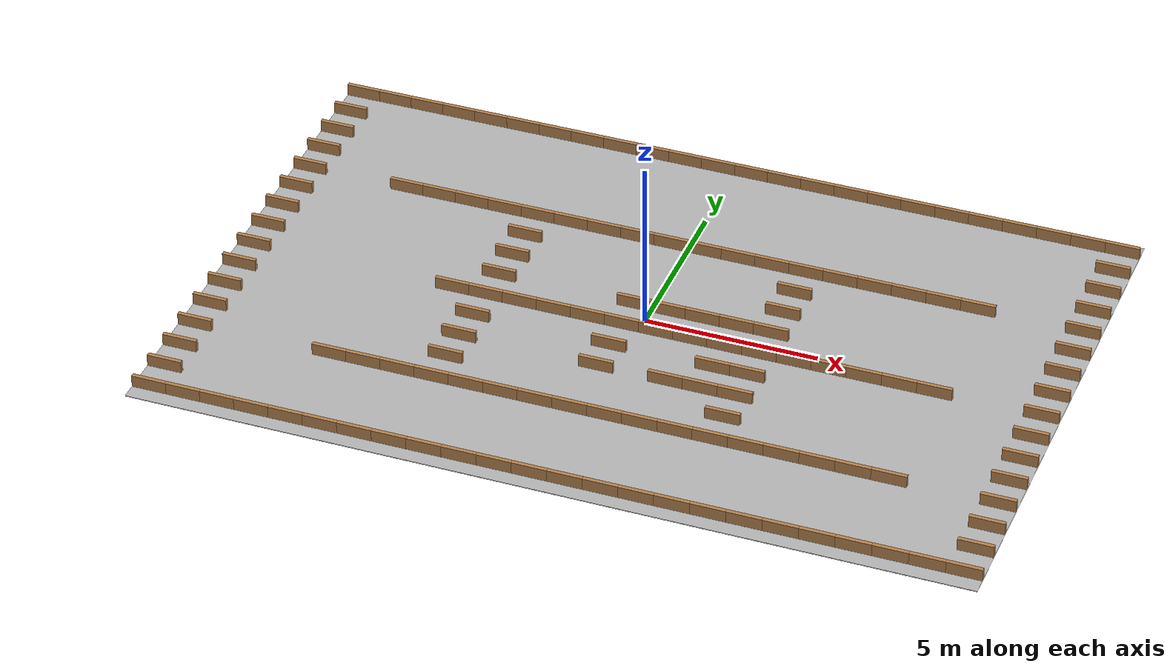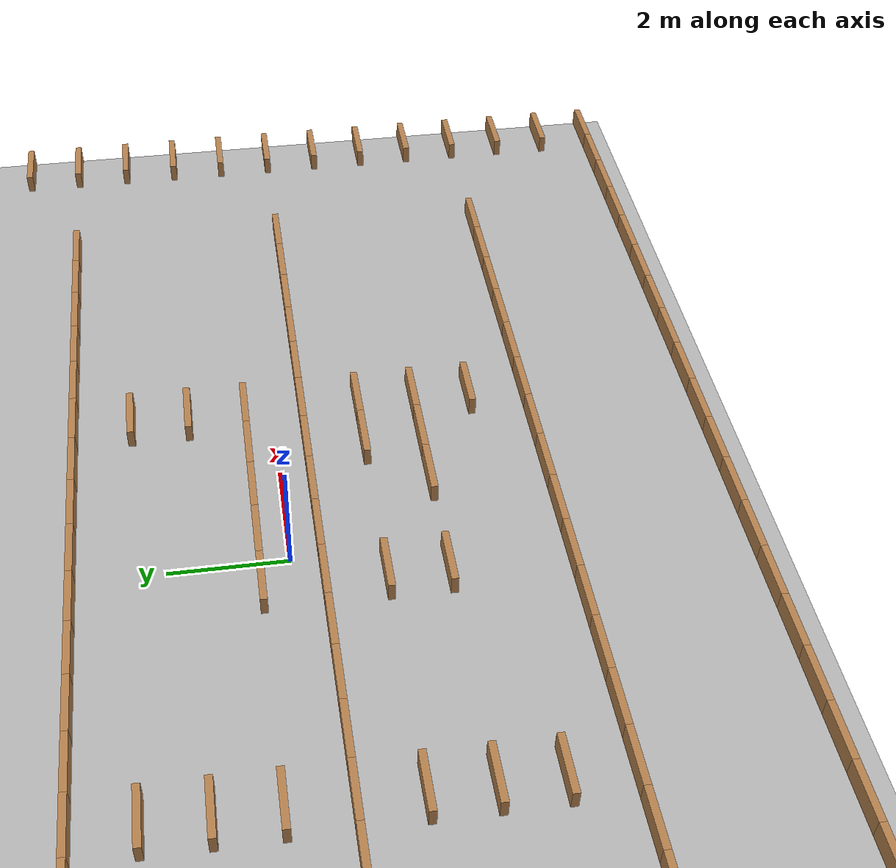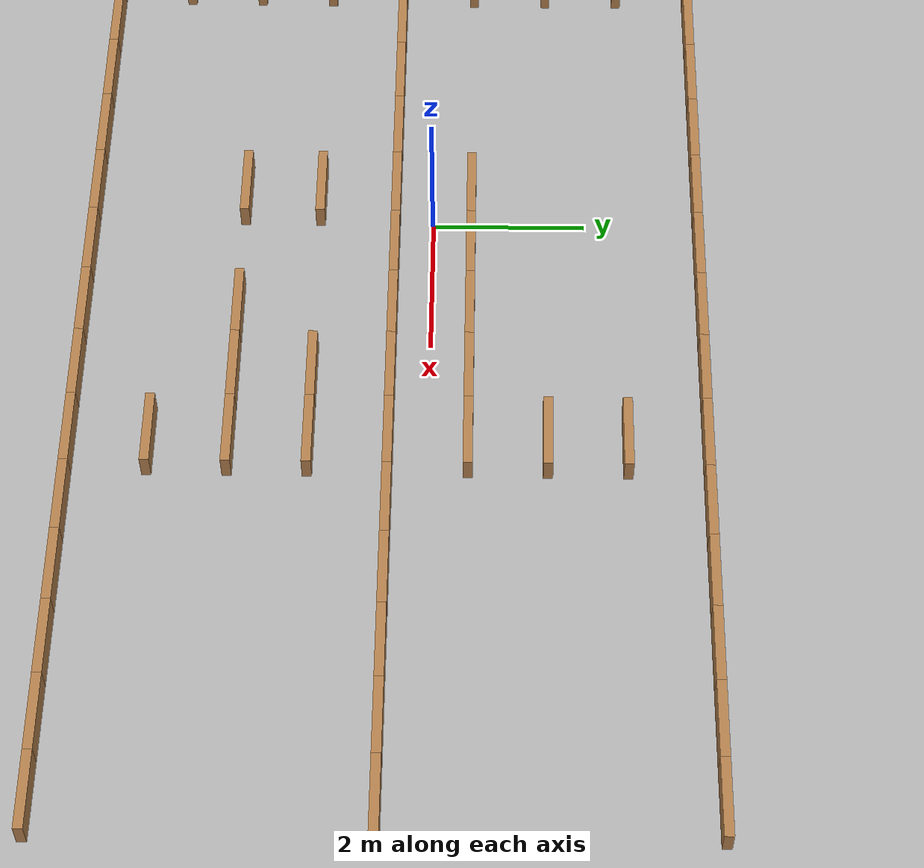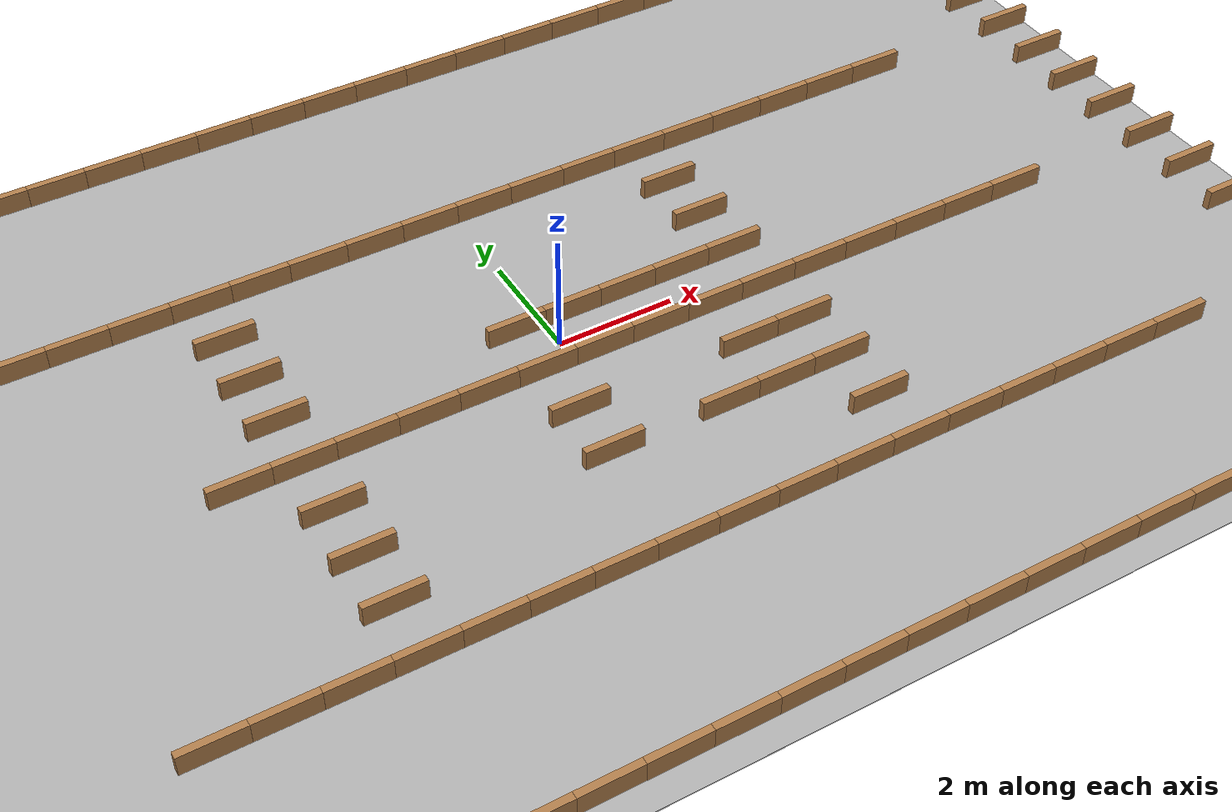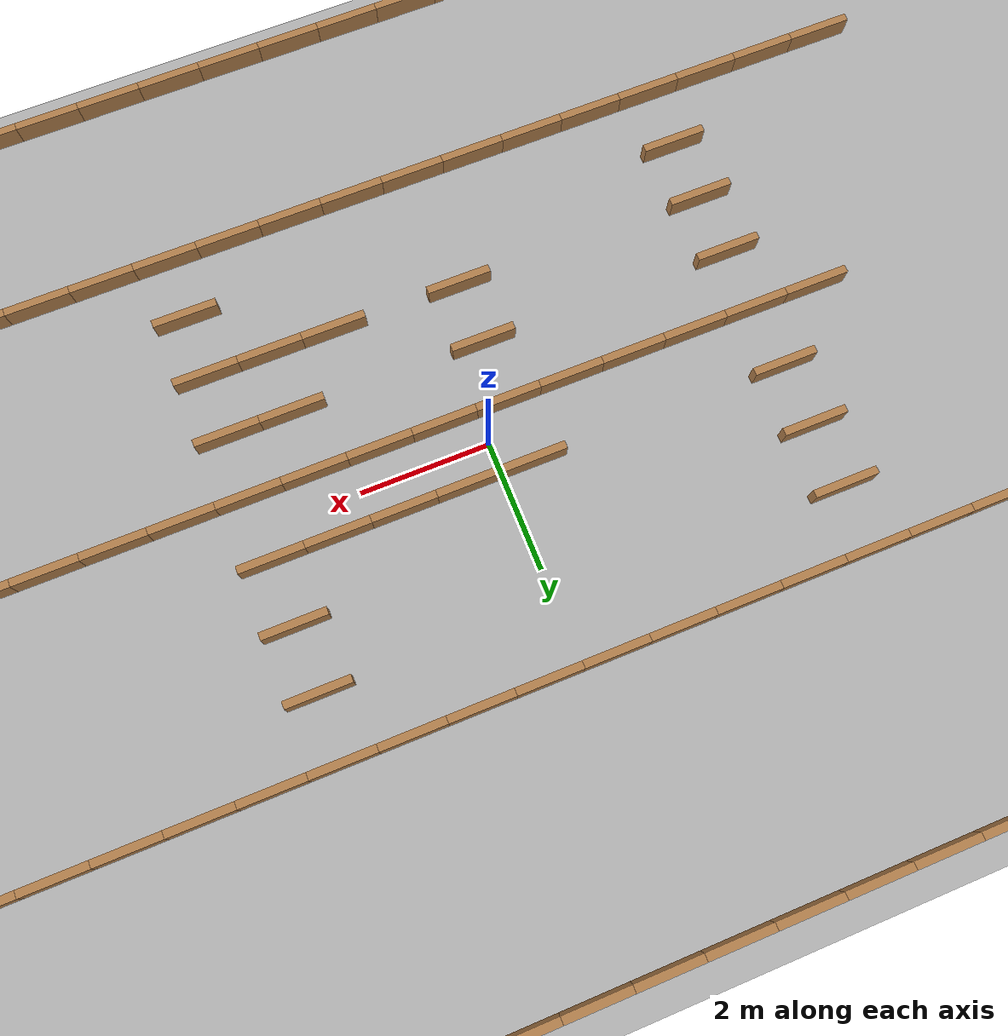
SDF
<?xml version='1.0'?>
<sdf version='1.7'>
  <world name='default'>
    <gravity>0 0 -9.81</gravity>

    <!-- Light -->
    <include><uri>model://sun</uri></include>

    <!-- Floor -->

    <model name='floor'>
      <pose>0 0 -0.01 0 0 0</pose>
      <static>true</static>
      <link name='link'>
        <collision name='col'>
          <geometry><box><size>24.0 16.0 0.02</size></box></geometry>
        </collision>
        <visual name='vis'>
          <geometry><box><size>24.0 16.0 0.02</size></box></geometry>
          <material><ambient>0.3 0.3 0.3 1</ambient><diffuse>0.7 0.7 0.7 1</diffuse><specular>0.1 0.1 0.1 1</specular></material>
        </visual>
      </link>
    </model>

    <model name='wall_r0_c0'>
      <pose>-11.5 7.5 0.175 0 0 0</pose>
      <static>true</static>
      <link name='link'>
        <collision name='col'>
          <geometry><box><size>1.0 0.12 0.35</size></box></geometry>
        </collision>
        <visual name='vis'>
          <geometry><box><size>1.0 0.12 0.35</size></box></geometry>
          <material><ambient>0.3 0.2 0.1 1</ambient><diffuse>0.7 0.5 0.3 1</diffuse><specular>0.1 0.1 0.1 1</specular></material>
        </visual>
      </link>
    </model>

    <model name='wall_r0_c1'>
      <pose>-10.5 7.5 0.175 0 0 0</pose>
      <static>true</static>
      <link name='link'>
        <collision name='col'>
          <geometry><box><size>1.0 0.12 0.35</size></box></geometry>
        </collision>
        <visual name='vis'>
          <geometry><box><size>1.0 0.12 0.35</size></box></geometry>
          <material><ambient>0.3 0.2 0.1 1</ambient><diffuse>0.7 0.5 0.3 1</diffuse><specular>0.1 0.1 0.1 1</specular></material>
        </visual>
      </link>
    </model>

    <model name='wall_r0_c2'>
      <pose>-9.5 7.5 0.175 0 0 0</pose>
      <static>true</static>
      <link name='link'>
        <collision name='col'>
          <geometry><box><size>1.0 0.12 0.35</size></box></geometry>
        </collision>
        <visual name='vis'>
          <geometry><box><size>1.0 0.12 0.35</size></box></geometry>
          <material><ambient>0.3 0.2 0.1 1</ambient><diffuse>0.7 0.5 0.3 1</diffuse><specular>0.1 0.1 0.1 1</specular></material>
        </visual>
      </link>
    </model>

    <model name='wall_r0_c3'>
      <pose>-8.5 7.5 0.175 0 0 0</pose>
      <static>true</static>
      <link name='link'>
        <collision name='col'>
          <geometry><box><size>1.0 0.12 0.35</size></box></geometry>
        </collision>
        <visual name='vis'>
          <geometry><box><size>1.0 0.12 0.35</size></box></geometry>
          <material><ambient>0.3 0.2 0.1 1</ambient><diffuse>0.7 0.5 0.3 1</diffuse><specular>0.1 0.1 0.1 1</specular></material>
        </visual>
      </link>
    </model>

    <model name='wall_r0_c4'>
      <pose>-7.5 7.5 0.175 0 0 0</pose>
      <static>true</static>
      <link name='link'>
        <collision name='col'>
          <geometry><box><size>1.0 0.12 0.35</size></box></geometry>
        </collision>
        <visual name='vis'>
          <geometry><box><size>1.0 0.12 0.35</size></box></geometry>
          <material><ambient>0.3 0.2 0.1 1</ambient><diffuse>0.7 0.5 0.3 1</diffuse><specular>0.1 0.1 0.1 1</specular></material>
        </visual>
      </link>
    </model>

    <model name='wall_r0_c5'>
      <pose>-6.5 7.5 0.175 0 0 0</pose>
      <static>true</static>
      <link name='link'>
        <collision name='col'>
          <geometry><box><size>1.0 0.12 0.35</size></box></geometry>
        </collision>
        <visual name='vis'>
          <geometry><box><size>1.0 0.12 0.35</size></box></geometry>
          <material><ambient>0.3 0.2 0.1 1</ambient><diffuse>0.7 0.5 0.3 1</diffuse><specular>0.1 0.1 0.1 1</specular></material>
        </visual>
      </link>
    </model>

    <model name='wall_r0_c6'>
      <pose>-5.5 7.5 0.175 0 0 0</pose>
      <static>true</static>
      <link name='link'>
        <collision name='col'>
          <geometry><box><size>1.0 0.12 0.35</size></box></geometry>
        </collision>
        <visual name='vis'>
          <geometry><box><size>1.0 0.12 0.35</size></box></geometry>
          <material><ambient>0.3 0.2 0.1 1</ambient><diffuse>0.7 0.5 0.3 1</diffuse><specular>0.1 0.1 0.1 1</specular></material>
        </visual>
      </link>
    </model>

    <model name='wall_r0_c7'>
      <pose>-4.5 7.5 0.175 0 0 0</pose>
      <static>true</static>
      <link name='link'>
        <collision name='col'>
          <geometry><box><size>1.0 0.12 0.35</size></box></geometry>
        </collision>
        <visual name='vis'>
          <geometry><box><size>1.0 0.12 0.35</size></box></geometry>
          <material><ambient>0.3 0.2 0.1 1</ambient><diffuse>0.7 0.5 0.3 1</diffuse><specular>0.1 0.1 0.1 1</specular></material>
        </visual>
      </link>
    </model>

    <model name='wall_r0_c8'>
      <pose>-3.5 7.5 0.175 0 0 0</pose>
      <static>true</static>
      <link name='link'>
        <collision name='col'>
          <geometry><box><size>1.0 0.12 0.35</size></box></geometry>
        </collision>
        <visual name='vis'>
          <geometry><box><size>1.0 0.12 0.35</size></box></geometry>
          <material><ambient>0.3 0.2 0.1 1</ambient><diffuse>0.7 0.5 0.3 1</diffuse><specular>0.1 0.1 0.1 1</specular></material>
        </visual>
      </link>
    </model>

    <model name='wall_r0_c9'>
      <pose>-2.5 7.5 0.175 0 0 0</pose>
      <static>true</static>
      <link name='link'>
        <collision name='col'>
          <geometry><box><size>1.0 0.12 0.35</size></box></geometry>
        </collision>
        <visual name='vis'>
          <geometry><box><size>1.0 0.12 0.35</size></box></geometry>
          <material><ambient>0.3 0.2 0.1 1</ambient><diffuse>0.7 0.5 0.3 1</diffuse><specular>0.1 0.1 0.1 1</specular></material>
        </visual>
      </link>
    </model>

    <model name='wall_r0_c10'>
      <pose>-1.5 7.5 0.175 0 0 0</pose>
      <static>true</static>
      <link name='link'>
        <collision name='col'>
          <geometry><box><size>1.0 0.12 0.35</size></box></geometry>
        </collision>
        <visual name='vis'>
          <geometry><box><size>1.0 0.12 0.35</size></box></geometry>
          <material><ambient>0.3 0.2 0.1 1</ambient><diffuse>0.7 0.5 0.3 1</diffuse><specular>0.1 0.1 0.1 1</specular></material>
        </visual>
      </link>
    </model>

    <model name='wall_r0_c11'>
      <pose>-0.5 7.5 0.175 0 0 0</pose>
      <static>true</static>
      <link name='link'>
        <collision name='col'>
          <geometry><box><size>1.0 0.12 0.35</size></box></geometry>
        </collision>
        <visual name='vis'>
          <geometry><box><size>1.0 0.12 0.35</size></box></geometry>
          <material><ambient>0.3 0.2 0.1 1</ambient><diffuse>0.7 0.5 0.3 1</diffuse><specular>0.1 0.1 0.1 1</specular></material>
        </visual>
      </link>
    </model>

    <model name='wall_r0_c12'>
      <pose>0.5 7.5 0.175 0 0 0</pose>
      <static>true</static>
      <link name='link'>
        <collision name='col'>
          <geometry><box><size>1.0 0.12 0.35</size></box></geometry>
        </collision>
        <visual name='vis'>
          <geometry><box><size>1.0 0.12 0.35</size></box></geometry>
          <material><ambient>0.3 0.2 0.1 1</ambient><diffuse>0.7 0.5 0.3 1</diffuse><specular>0.1 0.1 0.1 1</specular></material>
        </visual>
      </link>
    </model>

    <model name='wall_r0_c13'>
      <pose>1.5 7.5 0.175 0 0 0</pose>
      <static>true</static>
      <link name='link'>
        <collision name='col'>
          <geometry><box><size>1.0 0.12 0.35</size></box></geometry>
        </collision>
        <visual name='vis'>
          <geometry><box><size>1.0 0.12 0.35</size></box></geometry>
          <material><ambient>0.3 0.2 0.1 1</ambient><diffuse>0.7 0.5 0.3 1</diffuse><specular>0.1 0.1 0.1 1</specular></material>
        </visual>
      </link>
    </model>

    <model name='wall_r0_c14'>
      <pose>2.5 7.5 0.175 0 0 0</pose>
      <static>true</static>
      <link name='link'>
        <collision name='col'>
          <geometry><box><size>1.0 0.12 0.35</size></box></geometry>
        </collision>
        <visual name='vis'>
          <geometry><box><size>1.0 0.12 0.35</size></box></geometry>
          <material><ambient>0.3 0.2 0.1 1</ambient><diffuse>0.7 0.5 0.3 1</diffuse><specular>0.1 0.1 0.1 1</specular></material>
        </visual>
      </link>
    </model>

    <model name='wall_r0_c15'>
      <pose>3.5 7.5 0.175 0 0 0</pose>
      <static>true</static>
      <link name='link'>
        <collision name='col'>
          <geometry><box><size>1.0 0.12 0.35</size></box></geometry>
        </collision>
        <visual name='vis'>
          <geometry><box><size>1.0 0.12 0.35</size></box></geometry>
          <material><ambient>0.3 0.2 0.1 1</ambient><diffuse>0.7 0.5 0.3 1</diffuse><specular>0.1 0.1 0.1 1</specular></material>
        </visual>
      </link>
    </model>

    <model name='wall_r0_c16'>
      <pose>4.5 7.5 0.175 0 0 0</pose>
      <static>true</static>
      <link name='link'>
        <collision name='col'>
          <geometry><box><size>1.0 0.12 0.35</size></box></geometry>
        </collision>
        <visual name='vis'>
          <geometry><box><size>1.0 0.12 0.35</size></box></geometry>
          <material><ambient>0.3 0.2 0.1 1</ambient><diffuse>0.7 0.5 0.3 1</diffuse><specular>0.1 0.1 0.1 1</specular></material>
        </visual>
      </link>
    </model>

    <model name='wall_r0_c17'>
      <pose>5.5 7.5 0.175 0 0 0</pose>
      <static>true</static>
      <link name='link'>
        <collision name='col'>
          <geometry><box><size>1.0 0.12 0.35</size></box></geometry>
        </collision>
        <visual name='vis'>
          <geometry><box><size>1.0 0.12 0.35</size></box></geometry>
          <material><ambient>0.3 0.2 0.1 1</ambient><diffuse>0.7 0.5 0.3 1</diffuse><specular>0.1 0.1 0.1 1</specular></material>
        </visual>
      </link>
    </model>

    <model name='wall_r0_c18'>
      <pose>6.5 7.5 0.175 0 0 0</pose>
      <static>true</static>
      <link name='link'>
        <collision name='col'>
          <geometry><box><size>1.0 0.12 0.35</size></box></geometry>
        </collision>
        <visual name='vis'>
          <geometry><box><size>1.0 0.12 0.35</size></box></geometry>
          <material><ambient>0.3 0.2 0.1 1</ambient><diffuse>0.7 0.5 0.3 1</diffuse><specular>0.1 0.1 0.1 1</specular></material>
        </visual>
      </link>
    </model>

    <model name='wall_r0_c19'>
      <pose>7.5 7.5 0.175 0 0 0</pose>
      <static>true</static>
      <link name='link'>
        <collision name='col'>
          <geometry><box><size>1.0 0.12 0.35</size></box></geometry>
        </collision>
        <visual name='vis'>
          <geometry><box><size>1.0 0.12 0.35</size></box></geometry>
          <material><ambient>0.3 0.2 0.1 1</ambient><diffuse>0.7 0.5 0.3 1</diffuse><specular>0.1 0.1 0.1 1</specular></material>
        </visual>
      </link>
    </model>

    <model name='wall_r0_c20'>
      <pose>8.5 7.5 0.175 0 0 0</pose>
      <static>true</static>
      <link name='link'>
        <collision name='col'>
          <geometry><box><size>1.0 0.12 0.35</size></box></geometry>
        </collision>
        <visual name='vis'>
          <geometry><box><size>1.0 0.12 0.35</size></box></geometry>
          <material><ambient>0.3 0.2 0.1 1</ambient><diffuse>0.7 0.5 0.3 1</diffuse><specular>0.1 0.1 0.1 1</specular></material>
        </visual>
      </link>
    </model>

    <model name='wall_r0_c21'>
      <pose>9.5 7.5 0.175 0 0 0</pose>
      <static>true</static>
      <link name='link'>
        <collision name='col'>
          <geometry><box><size>1.0 0.12 0.35</size></box></geometry>
        </collision>
        <visual name='vis'>
          <geometry><box><size>1.0 0.12 0.35</size></box></geometry>
          <material><ambient>0.3 0.2 0.1 1</ambient><diffuse>0.7 0.5 0.3 1</diffuse><specular>0.1 0.1 0.1 1</specular></material>
        </visual>
      </link>
    </model>

    <model name='wall_r0_c22'>
      <pose>10.5 7.5 0.175 0 0 0</pose>
      <static>true</static>
      <link name='link'>
        <collision name='col'>
          <geometry><box><size>1.0 0.12 0.35</size></box></geometry>
        </collision>
        <visual name='vis'>
          <geometry><box><size>1.0 0.12 0.35</size></box></geometry>
          <material><ambient>0.3 0.2 0.1 1</ambient><diffuse>0.7 0.5 0.3 1</diffuse><specular>0.1 0.1 0.1 1</specular></material>
        </visual>
      </link>
    </model>

    <model name='wall_r0_c23'>
      <pose>11.5 7.5 0.175 0 0 0</pose>
      <static>true</static>
      <link name='link'>
        <collision name='col'>
          <geometry><box><size>1.0 0.12 0.35</size></box></geometry>
        </collision>
        <visual name='vis'>
          <geometry><box><size>1.0 0.12 0.35</size></box></geometry>
          <material><ambient>0.3 0.2 0.1 1</ambient><diffuse>0.7 0.5 0.3 1</diffuse><specular>0.1 0.1 0.1 1</specular></material>
        </visual>
      </link>
    </model>

    <model name='wall_r1_c0'>
      <pose>-11.5 6.5 0.175 0 0 0</pose>
      <static>true</static>
      <link name='link'>
        <collision name='col'>
          <geometry><box><size>1.0 0.12 0.35</size></box></geometry>
        </collision>
        <visual name='vis'>
          <geometry><box><size>1.0 0.12 0.35</size></box></geometry>
          <material><ambient>0.3 0.2 0.1 1</ambient><diffuse>0.7 0.5 0.3 1</diffuse><specular>0.1 0.1 0.1 1</specular></material>
        </visual>
      </link>
    </model>

    <model name='wall_r1_c23'>
      <pose>11.5 6.5 0.175 0 0 0</pose>
      <static>true</static>
      <link name='link'>
        <collision name='col'>
          <geometry><box><size>1.0 0.12 0.35</size></box></geometry>
        </collision>
        <visual name='vis'>
          <geometry><box><size>1.0 0.12 0.35</size></box></geometry>
          <material><ambient>0.3 0.2 0.1 1</ambient><diffuse>0.7 0.5 0.3 1</diffuse><specular>0.1 0.1 0.1 1</specular></material>
        </visual>
      </link>
    </model>

    <model name='wall_r2_c0'>
      <pose>-11.5 5.5 0.175 0 0 0</pose>
      <static>true</static>
      <link name='link'>
        <collision name='col'>
          <geometry><box><size>1.0 0.12 0.35</size></box></geometry>
        </collision>
        <visual name='vis'>
          <geometry><box><size>1.0 0.12 0.35</size></box></geometry>
          <material><ambient>0.3 0.2 0.1 1</ambient><diffuse>0.7 0.5 0.3 1</diffuse><specular>0.1 0.1 0.1 1</specular></material>
        </visual>
      </link>
    </model>

    <model name='wall_r2_c23'>
      <pose>11.5 5.5 0.175 0 0 0</pose>
      <static>true</static>
      <link name='link'>
        <collision name='col'>
          <geometry><box><size>1.0 0.12 0.35</size></box></geometry>
        </collision>
        <visual name='vis'>
          <geometry><box><size>1.0 0.12 0.35</size></box></geometry>
          <material><ambient>0.3 0.2 0.1 1</ambient><diffuse>0.7 0.5 0.3 1</diffuse><specular>0.1 0.1 0.1 1</specular></material>
        </visual>
      </link>
    </model>

    <model name='wall_r3_c0'>
      <pose>-11.5 4.5 0.175 0 0 0</pose>
      <static>true</static>
      <link name='link'>
        <collision name='col'>
          <geometry><box><size>1.0 0.12 0.35</size></box></geometry>
        </collision>
        <visual name='vis'>
          <geometry><box><size>1.0 0.12 0.35</size></box></geometry>
          <material><ambient>0.3 0.2 0.1 1</ambient><diffuse>0.7 0.5 0.3 1</diffuse><specular>0.1 0.1 0.1 1</specular></material>
        </visual>
      </link>
    </model>

    <model name='wall_r3_c23'>
      <pose>11.5 4.5 0.175 0 0 0</pose>
      <static>true</static>
      <link name='link'>
        <collision name='col'>
          <geometry><box><size>1.0 0.12 0.35</size></box></geometry>
        </collision>
        <visual name='vis'>
          <geometry><box><size>1.0 0.12 0.35</size></box></geometry>
          <material><ambient>0.3 0.2 0.1 1</ambient><diffuse>0.7 0.5 0.3 1</diffuse><specular>0.1 0.1 0.1 1</specular></material>
        </visual>
      </link>
    </model>

    <model name='wall_r4_c0'>
      <pose>-11.5 3.5 0.175 0 0 0</pose>
      <static>true</static>
      <link name='link'>
        <collision name='col'>
          <geometry><box><size>1.0 0.12 0.35</size></box></geometry>
        </collision>
        <visual name='vis'>
          <geometry><box><size>1.0 0.12 0.35</size></box></geometry>
          <material><ambient>0.3 0.2 0.1 1</ambient><diffuse>0.7 0.5 0.3 1</diffuse><specular>0.1 0.1 0.1 1</specular></material>
        </visual>
      </link>
    </model>

    <model name='wall_r4_c3'>
      <pose>-8.5 3.5 0.175 0 0 0</pose>
      <static>true</static>
      <link name='link'>
        <collision name='col'>
          <geometry><box><size>1.0 0.12 0.35</size></box></geometry>
        </collision>
        <visual name='vis'>
          <geometry><box><size>1.0 0.12 0.35</size></box></geometry>
          <material><ambient>0.3 0.2 0.1 1</ambient><diffuse>0.7 0.5 0.3 1</diffuse><specular>0.1 0.1 0.1 1</specular></material>
        </visual>
      </link>
    </model>

    <model name='wall_r4_c4'>
      <pose>-7.5 3.5 0.175 0 0 0</pose>
      <static>true</static>
      <link name='link'>
        <collision name='col'>
          <geometry><box><size>1.0 0.12 0.35</size></box></geometry>
        </collision>
        <visual name='vis'>
          <geometry><box><size>1.0 0.12 0.35</size></box></geometry>
          <material><ambient>0.3 0.2 0.1 1</ambient><diffuse>0.7 0.5 0.3 1</diffuse><specular>0.1 0.1 0.1 1</specular></material>
        </visual>
      </link>
    </model>

    <model name='wall_r4_c5'>
      <pose>-6.5 3.5 0.175 0 0 0</pose>
      <static>true</static>
      <link name='link'>
        <collision name='col'>
          <geometry><box><size>1.0 0.12 0.35</size></box></geometry>
        </collision>
        <visual name='vis'>
          <geometry><box><size>1.0 0.12 0.35</size></box></geometry>
          <material><ambient>0.3 0.2 0.1 1</ambient><diffuse>0.7 0.5 0.3 1</diffuse><specular>0.1 0.1 0.1 1</specular></material>
        </visual>
      </link>
    </model>

    <model name='wall_r4_c6'>
      <pose>-5.5 3.5 0.175 0 0 0</pose>
      <static>true</static>
      <link name='link'>
        <collision name='col'>
          <geometry><box><size>1.0 0.12 0.35</size></box></geometry>
        </collision>
        <visual name='vis'>
          <geometry><box><size>1.0 0.12 0.35</size></box></geometry>
          <material><ambient>0.3 0.2 0.1 1</ambient><diffuse>0.7 0.5 0.3 1</diffuse><specular>0.1 0.1 0.1 1</specular></material>
        </visual>
      </link>
    </model>

    <model name='wall_r4_c7'>
      <pose>-4.5 3.5 0.175 0 0 0</pose>
      <static>true</static>
      <link name='link'>
        <collision name='col'>
          <geometry><box><size>1.0 0.12 0.35</size></box></geometry>
        </collision>
        <visual name='vis'>
          <geometry><box><size>1.0 0.12 0.35</size></box></geometry>
          <material><ambient>0.3 0.2 0.1 1</ambient><diffuse>0.7 0.5 0.3 1</diffuse><specular>0.1 0.1 0.1 1</specular></material>
        </visual>
      </link>
    </model>

    <model name='wall_r4_c8'>
      <pose>-3.5 3.5 0.175 0 0 0</pose>
      <static>true</static>
      <link name='link'>
        <collision name='col'>
          <geometry><box><size>1.0 0.12 0.35</size></box></geometry>
        </collision>
        <visual name='vis'>
          <geometry><box><size>1.0 0.12 0.35</size></box></geometry>
          <material><ambient>0.3 0.2 0.1 1</ambient><diffuse>0.7 0.5 0.3 1</diffuse><specular>0.1 0.1 0.1 1</specular></material>
        </visual>
      </link>
    </model>

    <model name='wall_r4_c9'>
      <pose>-2.5 3.5 0.175 0 0 0</pose>
      <static>true</static>
      <link name='link'>
        <collision name='col'>
          <geometry><box><size>1.0 0.12 0.35</size></box></geometry>
        </collision>
        <visual name='vis'>
          <geometry><box><size>1.0 0.12 0.35</size></box></geometry>
          <material><ambient>0.3 0.2 0.1 1</ambient><diffuse>0.7 0.5 0.3 1</diffuse><specular>0.1 0.1 0.1 1</specular></material>
        </visual>
      </link>
    </model>

    <model name='wall_r4_c10'>
      <pose>-1.5 3.5 0.175 0 0 0</pose>
      <static>true</static>
      <link name='link'>
        <collision name='col'>
          <geometry><box><size>1.0 0.12 0.35</size></box></geometry>
        </collision>
        <visual name='vis'>
          <geometry><box><size>1.0 0.12 0.35</size></box></geometry>
          <material><ambient>0.3 0.2 0.1 1</ambient><diffuse>0.7 0.5 0.3 1</diffuse><specular>0.1 0.1 0.1 1</specular></material>
        </visual>
      </link>
    </model>

    <model name='wall_r4_c11'>
      <pose>-0.5 3.5 0.175 0 0 0</pose>
      <static>true</static>
      <link name='link'>
        <collision name='col'>
          <geometry><box><size>1.0 0.12 0.35</size></box></geometry>
        </collision>
        <visual name='vis'>
          <geometry><box><size>1.0 0.12 0.35</size></box></geometry>
          <material><ambient>0.3 0.2 0.1 1</ambient><diffuse>0.7 0.5 0.3 1</diffuse><specular>0.1 0.1 0.1 1</specular></material>
        </visual>
      </link>
    </model>

    <model name='wall_r4_c12'>
      <pose>0.5 3.5 0.175 0 0 0</pose>
      <static>true</static>
      <link name='link'>
        <collision name='col'>
          <geometry><box><size>1.0 0.12 0.35</size></box></geometry>
        </collision>
        <visual name='vis'>
          <geometry><box><size>1.0 0.12 0.35</size></box></geometry>
          <material><ambient>0.3 0.2 0.1 1</ambient><diffuse>0.7 0.5 0.3 1</diffuse><specular>0.1 0.1 0.1 1</specular></material>
        </visual>
      </link>
    </model>

    <model name='wall_r4_c13'>
      <pose>1.5 3.5 0.175 0 0 0</pose>
      <static>true</static>
      <link name='link'>
        <collision name='col'>
          <geometry><box><size>1.0 0.12 0.35</size></box></geometry>
        </collision>
        <visual name='vis'>
          <geometry><box><size>1.0 0.12 0.35</size></box></geometry>
          <material><ambient>0.3 0.2 0.1 1</ambient><diffuse>0.7 0.5 0.3 1</diffuse><specular>0.1 0.1 0.1 1</specular></material>
        </visual>
      </link>
    </model>

    <model name='wall_r4_c14'>
      <pose>2.5 3.5 0.175 0 0 0</pose>
      <static>true</static>
      <link name='link'>
        <collision name='col'>
          <geometry><box><size>1.0 0.12 0.35</size></box></geometry>
        </collision>
        <visual name='vis'>
          <geometry><box><size>1.0 0.12 0.35</size></box></geometry>
          <material><ambient>0.3 0.2 0.1 1</ambient><diffuse>0.7 0.5 0.3 1</diffuse><specular>0.1 0.1 0.1 1</specular></material>
        </visual>
      </link>
    </model>

    <model name='wall_r4_c15'>
      <pose>3.5 3.5 0.175 0 0 0</pose>
      <static>true</static>
      <link name='link'>
        <collision name='col'>
          <geometry><box><size>1.0 0.12 0.35</size></box></geometry>
        </collision>
        <visual name='vis'>
          <geometry><box><size>1.0 0.12 0.35</size></box></geometry>
          <material><ambient>0.3 0.2 0.1 1</ambient><diffuse>0.7 0.5 0.3 1</diffuse><specular>0.1 0.1 0.1 1</specular></material>
        </visual>
      </link>
    </model>

    <model name='wall_r4_c16'>
      <pose>4.5 3.5 0.175 0 0 0</pose>
      <static>true</static>
      <link name='link'>
        <collision name='col'>
          <geometry><box><size>1.0 0.12 0.35</size></box></geometry>
        </collision>
        <visual name='vis'>
          <geometry><box><size>1.0 0.12 0.35</size></box></geometry>
          <material><ambient>0.3 0.2 0.1 1</ambient><diffuse>0.7 0.5 0.3 1</diffuse><specular>0.1 0.1 0.1 1</specular></material>
        </visual>
      </link>
    </model>

    <model name='wall_r4_c17'>
      <pose>5.5 3.5 0.175 0 0 0</pose>
      <static>true</static>
      <link name='link'>
        <collision name='col'>
          <geometry><box><size>1.0 0.12 0.35</size></box></geometry>
        </collision>
        <visual name='vis'>
          <geometry><box><size>1.0 0.12 0.35</size></box></geometry>
          <material><ambient>0.3 0.2 0.1 1</ambient><diffuse>0.7 0.5 0.3 1</diffuse><specular>0.1 0.1 0.1 1</specular></material>
        </visual>
      </link>
    </model>

    <model name='wall_r4_c18'>
      <pose>6.5 3.5 0.175 0 0 0</pose>
      <static>true</static>
      <link name='link'>
        <collision name='col'>
          <geometry><box><size>1.0 0.12 0.35</size></box></geometry>
        </collision>
        <visual name='vis'>
          <geometry><box><size>1.0 0.12 0.35</size></box></geometry>
          <material><ambient>0.3 0.2 0.1 1</ambient><diffuse>0.7 0.5 0.3 1</diffuse><specular>0.1 0.1 0.1 1</specular></material>
        </visual>
      </link>
    </model>

    <model name='wall_r4_c19'>
      <pose>7.5 3.5 0.175 0 0 0</pose>
      <static>true</static>
      <link name='link'>
        <collision name='col'>
          <geometry><box><size>1.0 0.12 0.35</size></box></geometry>
        </collision>
        <visual name='vis'>
          <geometry><box><size>1.0 0.12 0.35</size></box></geometry>
          <material><ambient>0.3 0.2 0.1 1</ambient><diffuse>0.7 0.5 0.3 1</diffuse><specular>0.1 0.1 0.1 1</specular></material>
        </visual>
      </link>
    </model>

    <model name='wall_r4_c20'>
      <pose>8.5 3.5 0.175 0 0 0</pose>
      <static>true</static>
      <link name='link'>
        <collision name='col'>
          <geometry><box><size>1.0 0.12 0.35</size></box></geometry>
        </collision>
        <visual name='vis'>
          <geometry><box><size>1.0 0.12 0.35</size></box></geometry>
          <material><ambient>0.3 0.2 0.1 1</ambient><diffuse>0.7 0.5 0.3 1</diffuse><specular>0.1 0.1 0.1 1</specular></material>
        </visual>
      </link>
    </model>

    <model name='wall_r4_c23'>
      <pose>11.5 3.5 0.175 0 0 0</pose>
      <static>true</static>
      <link name='link'>
        <collision name='col'>
          <geometry><box><size>1.0 0.12 0.35</size></box></geometry>
        </collision>
        <visual name='vis'>
          <geometry><box><size>1.0 0.12 0.35</size></box></geometry>
          <material><ambient>0.3 0.2 0.1 1</ambient><diffuse>0.7 0.5 0.3 1</diffuse><specular>0.1 0.1 0.1 1</specular></material>
        </visual>
      </link>
    </model>

    <model name='wall_r5_c0'>
      <pose>-11.5 2.5 0.175 0 0 0</pose>
      <static>true</static>
      <link name='link'>
        <collision name='col'>
          <geometry><box><size>1.0 0.12 0.35</size></box></geometry>
        </collision>
        <visual name='vis'>
          <geometry><box><size>1.0 0.12 0.35</size></box></geometry>
          <material><ambient>0.3 0.2 0.1 1</ambient><diffuse>0.7 0.5 0.3 1</diffuse><specular>0.1 0.1 0.1 1</specular></material>
        </visual>
      </link>
    </model>

    <model name='wall_r5_c7'>
      <pose>-4.5 2.5 0.175 0 0 0</pose>
      <static>true</static>
      <link name='link'>
        <collision name='col'>
          <geometry><box><size>1.0 0.12 0.35</size></box></geometry>
        </collision>
        <visual name='vis'>
          <geometry><box><size>1.0 0.12 0.35</size></box></geometry>
          <material><ambient>0.3 0.2 0.1 1</ambient><diffuse>0.7 0.5 0.3 1</diffuse><specular>0.1 0.1 0.1 1</specular></material>
        </visual>
      </link>
    </model>

    <model name='wall_r5_c15'>
      <pose>3.5 2.5 0.175 0 0 0</pose>
      <static>true</static>
      <link name='link'>
        <collision name='col'>
          <geometry><box><size>1.0 0.12 0.35</size></box></geometry>
        </collision>
        <visual name='vis'>
          <geometry><box><size>1.0 0.12 0.35</size></box></geometry>
          <material><ambient>0.3 0.2 0.1 1</ambient><diffuse>0.7 0.5 0.3 1</diffuse><specular>0.1 0.1 0.1 1</specular></material>
        </visual>
      </link>
    </model>

    <model name='wall_r5_c23'>
      <pose>11.5 2.5 0.175 0 0 0</pose>
      <static>true</static>
      <link name='link'>
        <collision name='col'>
          <geometry><box><size>1.0 0.12 0.35</size></box></geometry>
        </collision>
        <visual name='vis'>
          <geometry><box><size>1.0 0.12 0.35</size></box></geometry>
          <material><ambient>0.3 0.2 0.1 1</ambient><diffuse>0.7 0.5 0.3 1</diffuse><specular>0.1 0.1 0.1 1</specular></material>
        </visual>
      </link>
    </model>

    <model name='wall_r6_c0'>
      <pose>-11.5 1.5 0.175 0 0 0</pose>
      <static>true</static>
      <link name='link'>
        <collision name='col'>
          <geometry><box><size>1.0 0.12 0.35</size></box></geometry>
        </collision>
        <visual name='vis'>
          <geometry><box><size>1.0 0.12 0.35</size></box></geometry>
          <material><ambient>0.3 0.2 0.1 1</ambient><diffuse>0.7 0.5 0.3 1</diffuse><specular>0.1 0.1 0.1 1</specular></material>
        </visual>
      </link>
    </model>

    <model name='wall_r6_c7'>
      <pose>-4.5 1.5 0.175 0 0 0</pose>
      <static>true</static>
      <link name='link'>
        <collision name='col'>
          <geometry><box><size>1.0 0.12 0.35</size></box></geometry>
        </collision>
        <visual name='vis'>
          <geometry><box><size>1.0 0.12 0.35</size></box></geometry>
          <material><ambient>0.3 0.2 0.1 1</ambient><diffuse>0.7 0.5 0.3 1</diffuse><specular>0.1 0.1 0.1 1</specular></material>
        </visual>
      </link>
    </model>

    <model name='wall_r6_c15'>
      <pose>3.5 1.5 0.175 0 0 0</pose>
      <static>true</static>
      <link name='link'>
        <collision name='col'>
          <geometry><box><size>1.0 0.12 0.35</size></box></geometry>
        </collision>
        <visual name='vis'>
          <geometry><box><size>1.0 0.12 0.35</size></box></geometry>
          <material><ambient>0.3 0.2 0.1 1</ambient><diffuse>0.7 0.5 0.3 1</diffuse><specular>0.1 0.1 0.1 1</specular></material>
        </visual>
      </link>
    </model>

    <model name='wall_r6_c23'>
      <pose>11.5 1.5 0.175 0 0 0</pose>
      <static>true</static>
      <link name='link'>
        <collision name='col'>
          <geometry><box><size>1.0 0.12 0.35</size></box></geometry>
        </collision>
        <visual name='vis'>
          <geometry><box><size>1.0 0.12 0.35</size></box></geometry>
          <material><ambient>0.3 0.2 0.1 1</ambient><diffuse>0.7 0.5 0.3 1</diffuse><specular>0.1 0.1 0.1 1</specular></material>
        </visual>
      </link>
    </model>

    <model name='wall_r7_c0'>
      <pose>-11.5 0.5 0.175 0 0 0</pose>
      <static>true</static>
      <link name='link'>
        <collision name='col'>
          <geometry><box><size>1.0 0.12 0.35</size></box></geometry>
        </collision>
        <visual name='vis'>
          <geometry><box><size>1.0 0.12 0.35</size></box></geometry>
          <material><ambient>0.3 0.2 0.1 1</ambient><diffuse>0.7 0.5 0.3 1</diffuse><specular>0.1 0.1 0.1 1</specular></material>
        </visual>
      </link>
    </model>

    <model name='wall_r7_c7'>
      <pose>-4.5 0.5 0.175 0 0 0</pose>
      <static>true</static>
      <link name='link'>
        <collision name='col'>
          <geometry><box><size>1.0 0.12 0.35</size></box></geometry>
        </collision>
        <visual name='vis'>
          <geometry><box><size>1.0 0.12 0.35</size></box></geometry>
          <material><ambient>0.3 0.2 0.1 1</ambient><diffuse>0.7 0.5 0.3 1</diffuse><specular>0.1 0.1 0.1 1</specular></material>
        </visual>
      </link>
    </model>

    <model name='wall_r7_c11'>
      <pose>-0.5 0.5 0.175 0 0 0</pose>
      <static>true</static>
      <link name='link'>
        <collision name='col'>
          <geometry><box><size>1.0 0.12 0.35</size></box></geometry>
        </collision>
        <visual name='vis'>
          <geometry><box><size>1.0 0.12 0.35</size></box></geometry>
          <material><ambient>0.3 0.2 0.1 1</ambient><diffuse>0.7 0.5 0.3 1</diffuse><specular>0.1 0.1 0.1 1</specular></material>
        </visual>
      </link>
    </model>

    <model name='wall_r7_c12'>
      <pose>0.5 0.5 0.175 0 0 0</pose>
      <static>true</static>
      <link name='link'>
        <collision name='col'>
          <geometry><box><size>1.0 0.12 0.35</size></box></geometry>
        </collision>
        <visual name='vis'>
          <geometry><box><size>1.0 0.12 0.35</size></box></geometry>
          <material><ambient>0.3 0.2 0.1 1</ambient><diffuse>0.7 0.5 0.3 1</diffuse><specular>0.1 0.1 0.1 1</specular></material>
        </visual>
      </link>
    </model>

    <model name='wall_r7_c13'>
      <pose>1.5 0.5 0.175 0 0 0</pose>
      <static>true</static>
      <link name='link'>
        <collision name='col'>
          <geometry><box><size>1.0 0.12 0.35</size></box></geometry>
        </collision>
        <visual name='vis'>
          <geometry><box><size>1.0 0.12 0.35</size></box></geometry>
          <material><ambient>0.3 0.2 0.1 1</ambient><diffuse>0.7 0.5 0.3 1</diffuse><specular>0.1 0.1 0.1 1</specular></material>
        </visual>
      </link>
    </model>

    <model name='wall_r7_c14'>
      <pose>2.5 0.5 0.175 0 0 0</pose>
      <static>true</static>
      <link name='link'>
        <collision name='col'>
          <geometry><box><size>1.0 0.12 0.35</size></box></geometry>
        </collision>
        <visual name='vis'>
          <geometry><box><size>1.0 0.12 0.35</size></box></geometry>
          <material><ambient>0.3 0.2 0.1 1</ambient><diffuse>0.7 0.5 0.3 1</diffuse><specular>0.1 0.1 0.1 1</specular></material>
        </visual>
      </link>
    </model>

    <model name='wall_r7_c15'>
      <pose>3.5 0.5 0.175 0 0 0</pose>
      <static>true</static>
      <link name='link'>
        <collision name='col'>
          <geometry><box><size>1.0 0.12 0.35</size></box></geometry>
        </collision>
        <visual name='vis'>
          <geometry><box><size>1.0 0.12 0.35</size></box></geometry>
          <material><ambient>0.3 0.2 0.1 1</ambient><diffuse>0.7 0.5 0.3 1</diffuse><specular>0.1 0.1 0.1 1</specular></material>
        </visual>
      </link>
    </model>

    <model name='wall_r7_c23'>
      <pose>11.5 0.5 0.175 0 0 0</pose>
      <static>true</static>
      <link name='link'>
        <collision name='col'>
          <geometry><box><size>1.0 0.12 0.35</size></box></geometry>
        </collision>
        <visual name='vis'>
          <geometry><box><size>1.0 0.12 0.35</size></box></geometry>
          <material><ambient>0.3 0.2 0.1 1</ambient><diffuse>0.7 0.5 0.3 1</diffuse><specular>0.1 0.1 0.1 1</specular></material>
        </visual>
      </link>
    </model>

    <model name='wall_r8_c0'>
      <pose>-11.5 -0.5 0.175 0 0 0</pose>
      <static>true</static>
      <link name='link'>
        <collision name='col'>
          <geometry><box><size>1.0 0.12 0.35</size></box></geometry>
        </collision>
        <visual name='vis'>
          <geometry><box><size>1.0 0.12 0.35</size></box></geometry>
          <material><ambient>0.3 0.2 0.1 1</ambient><diffuse>0.7 0.5 0.3 1</diffuse><specular>0.1 0.1 0.1 1</specular></material>
        </visual>
      </link>
    </model>

    <model name='wall_r8_c6'>
      <pose>-5.5 -0.5 0.175 0 0 0</pose>
      <static>true</static>
      <link name='link'>
        <collision name='col'>
          <geometry><box><size>1.0 0.12 0.35</size></box></geometry>
        </collision>
        <visual name='vis'>
          <geometry><box><size>1.0 0.12 0.35</size></box></geometry>
          <material><ambient>0.3 0.2 0.1 1</ambient><diffuse>0.7 0.5 0.3 1</diffuse><specular>0.1 0.1 0.1 1</specular></material>
        </visual>
      </link>
    </model>

    <model name='wall_r8_c7'>
      <pose>-4.5 -0.5 0.175 0 0 0</pose>
      <static>true</static>
      <link name='link'>
        <collision name='col'>
          <geometry><box><size>1.0 0.12 0.35</size></box></geometry>
        </collision>
        <visual name='vis'>
          <geometry><box><size>1.0 0.12 0.35</size></box></geometry>
          <material><ambient>0.3 0.2 0.1 1</ambient><diffuse>0.7 0.5 0.3 1</diffuse><specular>0.1 0.1 0.1 1</specular></material>
        </visual>
      </link>
    </model>

    <model name='wall_r8_c8'>
      <pose>-3.5 -0.5 0.175 0 0 0</pose>
      <static>true</static>
      <link name='link'>
        <collision name='col'>
          <geometry><box><size>1.0 0.12 0.35</size></box></geometry>
        </collision>
        <visual name='vis'>
          <geometry><box><size>1.0 0.12 0.35</size></box></geometry>
          <material><ambient>0.3 0.2 0.1 1</ambient><diffuse>0.7 0.5 0.3 1</diffuse><specular>0.1 0.1 0.1 1</specular></material>
        </visual>
      </link>
    </model>

    <model name='wall_r8_c9'>
      <pose>-2.5 -0.5 0.175 0 0 0</pose>
      <static>true</static>
      <link name='link'>
        <collision name='col'>
          <geometry><box><size>1.0 0.12 0.35</size></box></geometry>
        </collision>
        <visual name='vis'>
          <geometry><box><size>1.0 0.12 0.35</size></box></geometry>
          <material><ambient>0.3 0.2 0.1 1</ambient><diffuse>0.7 0.5 0.3 1</diffuse><specular>0.1 0.1 0.1 1</specular></material>
        </visual>
      </link>
    </model>

    <model name='wall_r8_c10'>
      <pose>-1.5 -0.5 0.175 0 0 0</pose>
      <static>true</static>
      <link name='link'>
        <collision name='col'>
          <geometry><box><size>1.0 0.12 0.35</size></box></geometry>
        </collision>
        <visual name='vis'>
          <geometry><box><size>1.0 0.12 0.35</size></box></geometry>
          <material><ambient>0.3 0.2 0.1 1</ambient><diffuse>0.7 0.5 0.3 1</diffuse><specular>0.1 0.1 0.1 1</specular></material>
        </visual>
      </link>
    </model>

    <model name='wall_r8_c11'>
      <pose>-0.5 -0.5 0.175 0 0 0</pose>
      <static>true</static>
      <link name='link'>
        <collision name='col'>
          <geometry><box><size>1.0 0.12 0.35</size></box></geometry>
        </collision>
        <visual name='vis'>
          <geometry><box><size>1.0 0.12 0.35</size></box></geometry>
          <material><ambient>0.3 0.2 0.1 1</ambient><diffuse>0.7 0.5 0.3 1</diffuse><specular>0.1 0.1 0.1 1</specular></material>
        </visual>
      </link>
    </model>

    <model name='wall_r8_c12'>
      <pose>0.5 -0.5 0.175 0 0 0</pose>
      <static>true</static>
      <link name='link'>
        <collision name='col'>
          <geometry><box><size>1.0 0.12 0.35</size></box></geometry>
        </collision>
        <visual name='vis'>
          <geometry><box><size>1.0 0.12 0.35</size></box></geometry>
          <material><ambient>0.3 0.2 0.1 1</ambient><diffuse>0.7 0.5 0.3 1</diffuse><specular>0.1 0.1 0.1 1</specular></material>
        </visual>
      </link>
    </model>

    <model name='wall_r8_c13'>
      <pose>1.5 -0.5 0.175 0 0 0</pose>
      <static>true</static>
      <link name='link'>
        <collision name='col'>
          <geometry><box><size>1.0 0.12 0.35</size></box></geometry>
        </collision>
        <visual name='vis'>
          <geometry><box><size>1.0 0.12 0.35</size></box></geometry>
          <material><ambient>0.3 0.2 0.1 1</ambient><diffuse>0.7 0.5 0.3 1</diffuse><specular>0.1 0.1 0.1 1</specular></material>
        </visual>
      </link>
    </model>

    <model name='wall_r8_c14'>
      <pose>2.5 -0.5 0.175 0 0 0</pose>
      <static>true</static>
      <link name='link'>
        <collision name='col'>
          <geometry><box><size>1.0 0.12 0.35</size></box></geometry>
        </collision>
        <visual name='vis'>
          <geometry><box><size>1.0 0.12 0.35</size></box></geometry>
          <material><ambient>0.3 0.2 0.1 1</ambient><diffuse>0.7 0.5 0.3 1</diffuse><specular>0.1 0.1 0.1 1</specular></material>
        </visual>
      </link>
    </model>

    <model name='wall_r8_c15'>
      <pose>3.5 -0.5 0.175 0 0 0</pose>
      <static>true</static>
      <link name='link'>
        <collision name='col'>
          <geometry><box><size>1.0 0.12 0.35</size></box></geometry>
        </collision>
        <visual name='vis'>
          <geometry><box><size>1.0 0.12 0.35</size></box></geometry>
          <material><ambient>0.3 0.2 0.1 1</ambient><diffuse>0.7 0.5 0.3 1</diffuse><specular>0.1 0.1 0.1 1</specular></material>
        </visual>
      </link>
    </model>

    <model name='wall_r8_c16'>
      <pose>4.5 -0.5 0.175 0 0 0</pose>
      <static>true</static>
      <link name='link'>
        <collision name='col'>
          <geometry><box><size>1.0 0.12 0.35</size></box></geometry>
        </collision>
        <visual name='vis'>
          <geometry><box><size>1.0 0.12 0.35</size></box></geometry>
          <material><ambient>0.3 0.2 0.1 1</ambient><diffuse>0.7 0.5 0.3 1</diffuse><specular>0.1 0.1 0.1 1</specular></material>
        </visual>
      </link>
    </model>

    <model name='wall_r8_c17'>
      <pose>5.5 -0.5 0.175 0 0 0</pose>
      <static>true</static>
      <link name='link'>
        <collision name='col'>
          <geometry><box><size>1.0 0.12 0.35</size></box></geometry>
        </collision>
        <visual name='vis'>
          <geometry><box><size>1.0 0.12 0.35</size></box></geometry>
          <material><ambient>0.3 0.2 0.1 1</ambient><diffuse>0.7 0.5 0.3 1</diffuse><specular>0.1 0.1 0.1 1</specular></material>
        </visual>
      </link>
    </model>

    <model name='wall_r8_c18'>
      <pose>6.5 -0.5 0.175 0 0 0</pose>
      <static>true</static>
      <link name='link'>
        <collision name='col'>
          <geometry><box><size>1.0 0.12 0.35</size></box></geometry>
        </collision>
        <visual name='vis'>
          <geometry><box><size>1.0 0.12 0.35</size></box></geometry>
          <material><ambient>0.3 0.2 0.1 1</ambient><diffuse>0.7 0.5 0.3 1</diffuse><specular>0.1 0.1 0.1 1</specular></material>
        </visual>
      </link>
    </model>

    <model name='wall_r8_c19'>
      <pose>7.5 -0.5 0.175 0 0 0</pose>
      <static>true</static>
      <link name='link'>
        <collision name='col'>
          <geometry><box><size>1.0 0.12 0.35</size></box></geometry>
        </collision>
        <visual name='vis'>
          <geometry><box><size>1.0 0.12 0.35</size></box></geometry>
          <material><ambient>0.3 0.2 0.1 1</ambient><diffuse>0.7 0.5 0.3 1</diffuse><specular>0.1 0.1 0.1 1</specular></material>
        </visual>
      </link>
    </model>

    <model name='wall_r8_c20'>
      <pose>8.5 -0.5 0.175 0 0 0</pose>
      <static>true</static>
      <link name='link'>
        <collision name='col'>
          <geometry><box><size>1.0 0.12 0.35</size></box></geometry>
        </collision>
        <visual name='vis'>
          <geometry><box><size>1.0 0.12 0.35</size></box></geometry>
          <material><ambient>0.3 0.2 0.1 1</ambient><diffuse>0.7 0.5 0.3 1</diffuse><specular>0.1 0.1 0.1 1</specular></material>
        </visual>
      </link>
    </model>

    <model name='wall_r8_c23'>
      <pose>11.5 -0.5 0.175 0 0 0</pose>
      <static>true</static>
      <link name='link'>
        <collision name='col'>
          <geometry><box><size>1.0 0.12 0.35</size></box></geometry>
        </collision>
        <visual name='vis'>
          <geometry><box><size>1.0 0.12 0.35</size></box></geometry>
          <material><ambient>0.3 0.2 0.1 1</ambient><diffuse>0.7 0.5 0.3 1</diffuse><specular>0.1 0.1 0.1 1</specular></material>
        </visual>
      </link>
    </model>

    <model name='wall_r9_c0'>
      <pose>-11.5 -1.5 0.175 0 0 0</pose>
      <static>true</static>
      <link name='link'>
        <collision name='col'>
          <geometry><box><size>1.0 0.12 0.35</size></box></geometry>
        </collision>
        <visual name='vis'>
          <geometry><box><size>1.0 0.12 0.35</size></box></geometry>
          <material><ambient>0.3 0.2 0.1 1</ambient><diffuse>0.7 0.5 0.3 1</diffuse><specular>0.1 0.1 0.1 1</specular></material>
        </visual>
      </link>
    </model>

    <model name='wall_r9_c7'>
      <pose>-4.5 -1.5 0.175 0 0 0</pose>
      <static>true</static>
      <link name='link'>
        <collision name='col'>
          <geometry><box><size>1.0 0.12 0.35</size></box></geometry>
        </collision>
        <visual name='vis'>
          <geometry><box><size>1.0 0.12 0.35</size></box></geometry>
          <material><ambient>0.3 0.2 0.1 1</ambient><diffuse>0.7 0.5 0.3 1</diffuse><specular>0.1 0.1 0.1 1</specular></material>
        </visual>
      </link>
    </model>

    <model name='wall_r9_c11'>
      <pose>-0.5 -1.5 0.175 0 0 0</pose>
      <static>true</static>
      <link name='link'>
        <collision name='col'>
          <geometry><box><size>1.0 0.12 0.35</size></box></geometry>
        </collision>
        <visual name='vis'>
          <geometry><box><size>1.0 0.12 0.35</size></box></geometry>
          <material><ambient>0.3 0.2 0.1 1</ambient><diffuse>0.7 0.5 0.3 1</diffuse><specular>0.1 0.1 0.1 1</specular></material>
        </visual>
      </link>
    </model>

    <model name='wall_r9_c14'>
      <pose>2.5 -1.5 0.175 0 0 0</pose>
      <static>true</static>
      <link name='link'>
        <collision name='col'>
          <geometry><box><size>1.0 0.12 0.35</size></box></geometry>
        </collision>
        <visual name='vis'>
          <geometry><box><size>1.0 0.12 0.35</size></box></geometry>
          <material><ambient>0.3 0.2 0.1 1</ambient><diffuse>0.7 0.5 0.3 1</diffuse><specular>0.1 0.1 0.1 1</specular></material>
        </visual>
      </link>
    </model>

    <model name='wall_r9_c15'>
      <pose>3.5 -1.5 0.175 0 0 0</pose>
      <static>true</static>
      <link name='link'>
        <collision name='col'>
          <geometry><box><size>1.0 0.12 0.35</size></box></geometry>
        </collision>
        <visual name='vis'>
          <geometry><box><size>1.0 0.12 0.35</size></box></geometry>
          <material><ambient>0.3 0.2 0.1 1</ambient><diffuse>0.7 0.5 0.3 1</diffuse><specular>0.1 0.1 0.1 1</specular></material>
        </visual>
      </link>
    </model>

    <model name='wall_r9_c23'>
      <pose>11.5 -1.5 0.175 0 0 0</pose>
      <static>true</static>
      <link name='link'>
        <collision name='col'>
          <geometry><box><size>1.0 0.12 0.35</size></box></geometry>
        </collision>
        <visual name='vis'>
          <geometry><box><size>1.0 0.12 0.35</size></box></geometry>
          <material><ambient>0.3 0.2 0.1 1</ambient><diffuse>0.7 0.5 0.3 1</diffuse><specular>0.1 0.1 0.1 1</specular></material>
        </visual>
      </link>
    </model>

    <model name='wall_r10_c0'>
      <pose>-11.5 -2.5 0.175 0 0 0</pose>
      <static>true</static>
      <link name='link'>
        <collision name='col'>
          <geometry><box><size>1.0 0.12 0.35</size></box></geometry>
        </collision>
        <visual name='vis'>
          <geometry><box><size>1.0 0.12 0.35</size></box></geometry>
          <material><ambient>0.3 0.2 0.1 1</ambient><diffuse>0.7 0.5 0.3 1</diffuse><specular>0.1 0.1 0.1 1</specular></material>
        </visual>
      </link>
    </model>

    <model name='wall_r10_c7'>
      <pose>-4.5 -2.5 0.175 0 0 0</pose>
      <static>true</static>
      <link name='link'>
        <collision name='col'>
          <geometry><box><size>1.0 0.12 0.35</size></box></geometry>
        </collision>
        <visual name='vis'>
          <geometry><box><size>1.0 0.12 0.35</size></box></geometry>
          <material><ambient>0.3 0.2 0.1 1</ambient><diffuse>0.7 0.5 0.3 1</diffuse><specular>0.1 0.1 0.1 1</specular></material>
        </visual>
      </link>
    </model>

    <model name='wall_r10_c11'>
      <pose>-0.5 -2.5 0.175 0 0 0</pose>
      <static>true</static>
      <link name='link'>
        <collision name='col'>
          <geometry><box><size>1.0 0.12 0.35</size></box></geometry>
        </collision>
        <visual name='vis'>
          <geometry><box><size>1.0 0.12 0.35</size></box></geometry>
          <material><ambient>0.3 0.2 0.1 1</ambient><diffuse>0.7 0.5 0.3 1</diffuse><specular>0.1 0.1 0.1 1</specular></material>
        </visual>
      </link>
    </model>

    <model name='wall_r10_c13'>
      <pose>1.5 -2.5 0.175 0 0 0</pose>
      <static>true</static>
      <link name='link'>
        <collision name='col'>
          <geometry><box><size>1.0 0.12 0.35</size></box></geometry>
        </collision>
        <visual name='vis'>
          <geometry><box><size>1.0 0.12 0.35</size></box></geometry>
          <material><ambient>0.3 0.2 0.1 1</ambient><diffuse>0.7 0.5 0.3 1</diffuse><specular>0.1 0.1 0.1 1</specular></material>
        </visual>
      </link>
    </model>

    <model name='wall_r10_c14'>
      <pose>2.5 -2.5 0.175 0 0 0</pose>
      <static>true</static>
      <link name='link'>
        <collision name='col'>
          <geometry><box><size>1.0 0.12 0.35</size></box></geometry>
        </collision>
        <visual name='vis'>
          <geometry><box><size>1.0 0.12 0.35</size></box></geometry>
          <material><ambient>0.3 0.2 0.1 1</ambient><diffuse>0.7 0.5 0.3 1</diffuse><specular>0.1 0.1 0.1 1</specular></material>
        </visual>
      </link>
    </model>

    <model name='wall_r10_c15'>
      <pose>3.5 -2.5 0.175 0 0 0</pose>
      <static>true</static>
      <link name='link'>
        <collision name='col'>
          <geometry><box><size>1.0 0.12 0.35</size></box></geometry>
        </collision>
        <visual name='vis'>
          <geometry><box><size>1.0 0.12 0.35</size></box></geometry>
          <material><ambient>0.3 0.2 0.1 1</ambient><diffuse>0.7 0.5 0.3 1</diffuse><specular>0.1 0.1 0.1 1</specular></material>
        </visual>
      </link>
    </model>

    <model name='wall_r10_c23'>
      <pose>11.5 -2.5 0.175 0 0 0</pose>
      <static>true</static>
      <link name='link'>
        <collision name='col'>
          <geometry><box><size>1.0 0.12 0.35</size></box></geometry>
        </collision>
        <visual name='vis'>
          <geometry><box><size>1.0 0.12 0.35</size></box></geometry>
          <material><ambient>0.3 0.2 0.1 1</ambient><diffuse>0.7 0.5 0.3 1</diffuse><specular>0.1 0.1 0.1 1</specular></material>
        </visual>
      </link>
    </model>

    <model name='wall_r11_c0'>
      <pose>-11.5 -3.5 0.175 0 0 0</pose>
      <static>true</static>
      <link name='link'>
        <collision name='col'>
          <geometry><box><size>1.0 0.12 0.35</size></box></geometry>
        </collision>
        <visual name='vis'>
          <geometry><box><size>1.0 0.12 0.35</size></box></geometry>
          <material><ambient>0.3 0.2 0.1 1</ambient><diffuse>0.7 0.5 0.3 1</diffuse><specular>0.1 0.1 0.1 1</specular></material>
        </visual>
      </link>
    </model>

    <model name='wall_r11_c7'>
      <pose>-4.5 -3.5 0.175 0 0 0</pose>
      <static>true</static>
      <link name='link'>
        <collision name='col'>
          <geometry><box><size>1.0 0.12 0.35</size></box></geometry>
        </collision>
        <visual name='vis'>
          <geometry><box><size>1.0 0.12 0.35</size></box></geometry>
          <material><ambient>0.3 0.2 0.1 1</ambient><diffuse>0.7 0.5 0.3 1</diffuse><specular>0.1 0.1 0.1 1</specular></material>
        </visual>
      </link>
    </model>

    <model name='wall_r11_c15'>
      <pose>3.5 -3.5 0.175 0 0 0</pose>
      <static>true</static>
      <link name='link'>
        <collision name='col'>
          <geometry><box><size>1.0 0.12 0.35</size></box></geometry>
        </collision>
        <visual name='vis'>
          <geometry><box><size>1.0 0.12 0.35</size></box></geometry>
          <material><ambient>0.3 0.2 0.1 1</ambient><diffuse>0.7 0.5 0.3 1</diffuse><specular>0.1 0.1 0.1 1</specular></material>
        </visual>
      </link>
    </model>

    <model name='wall_r11_c23'>
      <pose>11.5 -3.5 0.175 0 0 0</pose>
      <static>true</static>
      <link name='link'>
        <collision name='col'>
          <geometry><box><size>1.0 0.12 0.35</size></box></geometry>
        </collision>
        <visual name='vis'>
          <geometry><box><size>1.0 0.12 0.35</size></box></geometry>
          <material><ambient>0.3 0.2 0.1 1</ambient><diffuse>0.7 0.5 0.3 1</diffuse><specular>0.1 0.1 0.1 1</specular></material>
        </visual>
      </link>
    </model>

    <model name='wall_r12_c0'>
      <pose>-11.5 -4.5 0.175 0 0 0</pose>
      <static>true</static>
      <link name='link'>
        <collision name='col'>
          <geometry><box><size>1.0 0.12 0.35</size></box></geometry>
        </collision>
        <visual name='vis'>
          <geometry><box><size>1.0 0.12 0.35</size></box></geometry>
          <material><ambient>0.3 0.2 0.1 1</ambient><diffuse>0.7 0.5 0.3 1</diffuse><specular>0.1 0.1 0.1 1</specular></material>
        </visual>
      </link>
    </model>

    <model name='wall_r12_c4'>
      <pose>-7.5 -4.5 0.175 0 0 0</pose>
      <static>true</static>
      <link name='link'>
        <collision name='col'>
          <geometry><box><size>1.0 0.12 0.35</size></box></geometry>
        </collision>
        <visual name='vis'>
          <geometry><box><size>1.0 0.12 0.35</size></box></geometry>
          <material><ambient>0.3 0.2 0.1 1</ambient><diffuse>0.7 0.5 0.3 1</diffuse><specular>0.1 0.1 0.1 1</specular></material>
        </visual>
      </link>
    </model>

    <model name='wall_r12_c5'>
      <pose>-6.5 -4.5 0.175 0 0 0</pose>
      <static>true</static>
      <link name='link'>
        <collision name='col'>
          <geometry><box><size>1.0 0.12 0.35</size></box></geometry>
        </collision>
        <visual name='vis'>
          <geometry><box><size>1.0 0.12 0.35</size></box></geometry>
          <material><ambient>0.3 0.2 0.1 1</ambient><diffuse>0.7 0.5 0.3 1</diffuse><specular>0.1 0.1 0.1 1</specular></material>
        </visual>
      </link>
    </model>

    <model name='wall_r12_c6'>
      <pose>-5.5 -4.5 0.175 0 0 0</pose>
      <static>true</static>
      <link name='link'>
        <collision name='col'>
          <geometry><box><size>1.0 0.12 0.35</size></box></geometry>
        </collision>
        <visual name='vis'>
          <geometry><box><size>1.0 0.12 0.35</size></box></geometry>
          <material><ambient>0.3 0.2 0.1 1</ambient><diffuse>0.7 0.5 0.3 1</diffuse><specular>0.1 0.1 0.1 1</specular></material>
        </visual>
      </link>
    </model>

    <model name='wall_r12_c7'>
      <pose>-4.5 -4.5 0.175 0 0 0</pose>
      <static>true</static>
      <link name='link'>
        <collision name='col'>
          <geometry><box><size>1.0 0.12 0.35</size></box></geometry>
        </collision>
        <visual name='vis'>
          <geometry><box><size>1.0 0.12 0.35</size></box></geometry>
          <material><ambient>0.3 0.2 0.1 1</ambient><diffuse>0.7 0.5 0.3 1</diffuse><specular>0.1 0.1 0.1 1</specular></material>
        </visual>
      </link>
    </model>

    <model name='wall_r12_c8'>
      <pose>-3.5 -4.5 0.175 0 0 0</pose>
      <static>true</static>
      <link name='link'>
        <collision name='col'>
          <geometry><box><size>1.0 0.12 0.35</size></box></geometry>
        </collision>
        <visual name='vis'>
          <geometry><box><size>1.0 0.12 0.35</size></box></geometry>
          <material><ambient>0.3 0.2 0.1 1</ambient><diffuse>0.7 0.5 0.3 1</diffuse><specular>0.1 0.1 0.1 1</specular></material>
        </visual>
      </link>
    </model>

    <model name='wall_r12_c9'>
      <pose>-2.5 -4.5 0.175 0 0 0</pose>
      <static>true</static>
      <link name='link'>
        <collision name='col'>
          <geometry><box><size>1.0 0.12 0.35</size></box></geometry>
        </collision>
        <visual name='vis'>
          <geometry><box><size>1.0 0.12 0.35</size></box></geometry>
          <material><ambient>0.3 0.2 0.1 1</ambient><diffuse>0.7 0.5 0.3 1</diffuse><specular>0.1 0.1 0.1 1</specular></material>
        </visual>
      </link>
    </model>

    <model name='wall_r12_c10'>
      <pose>-1.5 -4.5 0.175 0 0 0</pose>
      <static>true</static>
      <link name='link'>
        <collision name='col'>
          <geometry><box><size>1.0 0.12 0.35</size></box></geometry>
        </collision>
        <visual name='vis'>
          <geometry><box><size>1.0 0.12 0.35</size></box></geometry>
          <material><ambient>0.3 0.2 0.1 1</ambient><diffuse>0.7 0.5 0.3 1</diffuse><specular>0.1 0.1 0.1 1</specular></material>
        </visual>
      </link>
    </model>

    <model name='wall_r12_c11'>
      <pose>-0.5 -4.5 0.175 0 0 0</pose>
      <static>true</static>
      <link name='link'>
        <collision name='col'>
          <geometry><box><size>1.0 0.12 0.35</size></box></geometry>
        </collision>
        <visual name='vis'>
          <geometry><box><size>1.0 0.12 0.35</size></box></geometry>
          <material><ambient>0.3 0.2 0.1 1</ambient><diffuse>0.7 0.5 0.3 1</diffuse><specular>0.1 0.1 0.1 1</specular></material>
        </visual>
      </link>
    </model>

    <model name='wall_r12_c12'>
      <pose>0.5 -4.5 0.175 0 0 0</pose>
      <static>true</static>
      <link name='link'>
        <collision name='col'>
          <geometry><box><size>1.0 0.12 0.35</size></box></geometry>
        </collision>
        <visual name='vis'>
          <geometry><box><size>1.0 0.12 0.35</size></box></geometry>
          <material><ambient>0.3 0.2 0.1 1</ambient><diffuse>0.7 0.5 0.3 1</diffuse><specular>0.1 0.1 0.1 1</specular></material>
        </visual>
      </link>
    </model>

    <model name='wall_r12_c13'>
      <pose>1.5 -4.5 0.175 0 0 0</pose>
      <static>true</static>
      <link name='link'>
        <collision name='col'>
          <geometry><box><size>1.0 0.12 0.35</size></box></geometry>
        </collision>
        <visual name='vis'>
          <geometry><box><size>1.0 0.12 0.35</size></box></geometry>
          <material><ambient>0.3 0.2 0.1 1</ambient><diffuse>0.7 0.5 0.3 1</diffuse><specular>0.1 0.1 0.1 1</specular></material>
        </visual>
      </link>
    </model>

    <model name='wall_r12_c14'>
      <pose>2.5 -4.5 0.175 0 0 0</pose>
      <static>true</static>
      <link name='link'>
        <collision name='col'>
          <geometry><box><size>1.0 0.12 0.35</size></box></geometry>
        </collision>
        <visual name='vis'>
          <geometry><box><size>1.0 0.12 0.35</size></box></geometry>
          <material><ambient>0.3 0.2 0.1 1</ambient><diffuse>0.7 0.5 0.3 1</diffuse><specular>0.1 0.1 0.1 1</specular></material>
        </visual>
      </link>
    </model>

    <model name='wall_r12_c15'>
      <pose>3.5 -4.5 0.175 0 0 0</pose>
      <static>true</static>
      <link name='link'>
        <collision name='col'>
          <geometry><box><size>1.0 0.12 0.35</size></box></geometry>
        </collision>
        <visual name='vis'>
          <geometry><box><size>1.0 0.12 0.35</size></box></geometry>
          <material><ambient>0.3 0.2 0.1 1</ambient><diffuse>0.7 0.5 0.3 1</diffuse><specular>0.1 0.1 0.1 1</specular></material>
        </visual>
      </link>
    </model>

    <model name='wall_r12_c16'>
      <pose>4.5 -4.5 0.175 0 0 0</pose>
      <static>true</static>
      <link name='link'>
        <collision name='col'>
          <geometry><box><size>1.0 0.12 0.35</size></box></geometry>
        </collision>
        <visual name='vis'>
          <geometry><box><size>1.0 0.12 0.35</size></box></geometry>
          <material><ambient>0.3 0.2 0.1 1</ambient><diffuse>0.7 0.5 0.3 1</diffuse><specular>0.1 0.1 0.1 1</specular></material>
        </visual>
      </link>
    </model>

    <model name='wall_r12_c17'>
      <pose>5.5 -4.5 0.175 0 0 0</pose>
      <static>true</static>
      <link name='link'>
        <collision name='col'>
          <geometry><box><size>1.0 0.12 0.35</size></box></geometry>
        </collision>
        <visual name='vis'>
          <geometry><box><size>1.0 0.12 0.35</size></box></geometry>
          <material><ambient>0.3 0.2 0.1 1</ambient><diffuse>0.7 0.5 0.3 1</diffuse><specular>0.1 0.1 0.1 1</specular></material>
        </visual>
      </link>
    </model>

    <model name='wall_r12_c18'>
      <pose>6.5 -4.5 0.175 0 0 0</pose>
      <static>true</static>
      <link name='link'>
        <collision name='col'>
          <geometry><box><size>1.0 0.12 0.35</size></box></geometry>
        </collision>
        <visual name='vis'>
          <geometry><box><size>1.0 0.12 0.35</size></box></geometry>
          <material><ambient>0.3 0.2 0.1 1</ambient><diffuse>0.7 0.5 0.3 1</diffuse><specular>0.1 0.1 0.1 1</specular></material>
        </visual>
      </link>
    </model>

    <model name='wall_r12_c19'>
      <pose>7.5 -4.5 0.175 0 0 0</pose>
      <static>true</static>
      <link name='link'>
        <collision name='col'>
          <geometry><box><size>1.0 0.12 0.35</size></box></geometry>
        </collision>
        <visual name='vis'>
          <geometry><box><size>1.0 0.12 0.35</size></box></geometry>
          <material><ambient>0.3 0.2 0.1 1</ambient><diffuse>0.7 0.5 0.3 1</diffuse><specular>0.1 0.1 0.1 1</specular></material>
        </visual>
      </link>
    </model>

    <model name='wall_r12_c20'>
      <pose>8.5 -4.5 0.175 0 0 0</pose>
      <static>true</static>
      <link name='link'>
        <collision name='col'>
          <geometry><box><size>1.0 0.12 0.35</size></box></geometry>
        </collision>
        <visual name='vis'>
          <geometry><box><size>1.0 0.12 0.35</size></box></geometry>
          <material><ambient>0.3 0.2 0.1 1</ambient><diffuse>0.7 0.5 0.3 1</diffuse><specular>0.1 0.1 0.1 1</specular></material>
        </visual>
      </link>
    </model>

    <model name='wall_r12_c23'>
      <pose>11.5 -4.5 0.175 0 0 0</pose>
      <static>true</static>
      <link name='link'>
        <collision name='col'>
          <geometry><box><size>1.0 0.12 0.35</size></box></geometry>
        </collision>
        <visual name='vis'>
          <geometry><box><size>1.0 0.12 0.35</size></box></geometry>
          <material><ambient>0.3 0.2 0.1 1</ambient><diffuse>0.7 0.5 0.3 1</diffuse><specular>0.1 0.1 0.1 1</specular></material>
        </visual>
      </link>
    </model>

    <model name='wall_r13_c0'>
      <pose>-11.5 -5.5 0.175 0 0 0</pose>
      <static>true</static>
      <link name='link'>
        <collision name='col'>
          <geometry><box><size>1.0 0.12 0.35</size></box></geometry>
        </collision>
        <visual name='vis'>
          <geometry><box><size>1.0 0.12 0.35</size></box></geometry>
          <material><ambient>0.3 0.2 0.1 1</ambient><diffuse>0.7 0.5 0.3 1</diffuse><specular>0.1 0.1 0.1 1</specular></material>
        </visual>
      </link>
    </model>

    <model name='wall_r13_c23'>
      <pose>11.5 -5.5 0.175 0 0 0</pose>
      <static>true</static>
      <link name='link'>
        <collision name='col'>
          <geometry><box><size>1.0 0.12 0.35</size></box></geometry>
        </collision>
        <visual name='vis'>
          <geometry><box><size>1.0 0.12 0.35</size></box></geometry>
          <material><ambient>0.3 0.2 0.1 1</ambient><diffuse>0.7 0.5 0.3 1</diffuse><specular>0.1 0.1 0.1 1</specular></material>
        </visual>
      </link>
    </model>

    <model name='wall_r14_c0'>
      <pose>-11.5 -6.5 0.175 0 0 0</pose>
      <static>true</static>
      <link name='link'>
        <collision name='col'>
          <geometry><box><size>1.0 0.12 0.35</size></box></geometry>
        </collision>
        <visual name='vis'>
          <geometry><box><size>1.0 0.12 0.35</size></box></geometry>
          <material><ambient>0.3 0.2 0.1 1</ambient><diffuse>0.7 0.5 0.3 1</diffuse><specular>0.1 0.1 0.1 1</specular></material>
        </visual>
      </link>
    </model>

    <model name='wall_r14_c23'>
      <pose>11.5 -6.5 0.175 0 0 0</pose>
      <static>true</static>
      <link name='link'>
        <collision name='col'>
          <geometry><box><size>1.0 0.12 0.35</size></box></geometry>
        </collision>
        <visual name='vis'>
          <geometry><box><size>1.0 0.12 0.35</size></box></geometry>
          <material><ambient>0.3 0.2 0.1 1</ambient><diffuse>0.7 0.5 0.3 1</diffuse><specular>0.1 0.1 0.1 1</specular></material>
        </visual>
      </link>
    </model>

    <model name='wall_r15_c0'>
      <pose>-11.5 -7.5 0.175 0 0 0</pose>
      <static>true</static>
      <link name='link'>
        <collision name='col'>
          <geometry><box><size>1.0 0.12 0.35</size></box></geometry>
        </collision>
        <visual name='vis'>
          <geometry><box><size>1.0 0.12 0.35</size></box></geometry>
          <material><ambient>0.3 0.2 0.1 1</ambient><diffuse>0.7 0.5 0.3 1</diffuse><specular>0.1 0.1 0.1 1</specular></material>
        </visual>
      </link>
    </model>

    <model name='wall_r15_c1'>
      <pose>-10.5 -7.5 0.175 0 0 0</pose>
      <static>true</static>
      <link name='link'>
        <collision name='col'>
          <geometry><box><size>1.0 0.12 0.35</size></box></geometry>
        </collision>
        <visual name='vis'>
          <geometry><box><size>1.0 0.12 0.35</size></box></geometry>
          <material><ambient>0.3 0.2 0.1 1</ambient><diffuse>0.7 0.5 0.3 1</diffuse><specular>0.1 0.1 0.1 1</specular></material>
        </visual>
      </link>
    </model>

    <model name='wall_r15_c2'>
      <pose>-9.5 -7.5 0.175 0 0 0</pose>
      <static>true</static>
      <link name='link'>
        <collision name='col'>
          <geometry><box><size>1.0 0.12 0.35</size></box></geometry>
        </collision>
        <visual name='vis'>
          <geometry><box><size>1.0 0.12 0.35</size></box></geometry>
          <material><ambient>0.3 0.2 0.1 1</ambient><diffuse>0.7 0.5 0.3 1</diffuse><specular>0.1 0.1 0.1 1</specular></material>
        </visual>
      </link>
    </model>

    <model name='wall_r15_c3'>
      <pose>-8.5 -7.5 0.175 0 0 0</pose>
      <static>true</static>
      <link name='link'>
        <collision name='col'>
          <geometry><box><size>1.0 0.12 0.35</size></box></geometry>
        </collision>
        <visual name='vis'>
          <geometry><box><size>1.0 0.12 0.35</size></box></geometry>
          <material><ambient>0.3 0.2 0.1 1</ambient><diffuse>0.7 0.5 0.3 1</diffuse><specular>0.1 0.1 0.1 1</specular></material>
        </visual>
      </link>
    </model>

    <model name='wall_r15_c4'>
      <pose>-7.5 -7.5 0.175 0 0 0</pose>
      <static>true</static>
      <link name='link'>
        <collision name='col'>
          <geometry><box><size>1.0 0.12 0.35</size></box></geometry>
        </collision>
        <visual name='vis'>
          <geometry><box><size>1.0 0.12 0.35</size></box></geometry>
          <material><ambient>0.3 0.2 0.1 1</ambient><diffuse>0.7 0.5 0.3 1</diffuse><specular>0.1 0.1 0.1 1</specular></material>
        </visual>
      </link>
    </model>

    <model name='wall_r15_c5'>
      <pose>-6.5 -7.5 0.175 0 0 0</pose>
      <static>true</static>
      <link name='link'>
        <collision name='col'>
          <geometry><box><size>1.0 0.12 0.35</size></box></geometry>
        </collision>
        <visual name='vis'>
          <geometry><box><size>1.0 0.12 0.35</size></box></geometry>
          <material><ambient>0.3 0.2 0.1 1</ambient><diffuse>0.7 0.5 0.3 1</diffuse><specular>0.1 0.1 0.1 1</specular></material>
        </visual>
      </link>
    </model>

    <model name='wall_r15_c6'>
      <pose>-5.5 -7.5 0.175 0 0 0</pose>
      <static>true</static>
      <link name='link'>
        <collision name='col'>
          <geometry><box><size>1.0 0.12 0.35</size></box></geometry>
        </collision>
        <visual name='vis'>
          <geometry><box><size>1.0 0.12 0.35</size></box></geometry>
          <material><ambient>0.3 0.2 0.1 1</ambient><diffuse>0.7 0.5 0.3 1</diffuse><specular>0.1 0.1 0.1 1</specular></material>
        </visual>
      </link>
    </model>

    <model name='wall_r15_c7'>
      <pose>-4.5 -7.5 0.175 0 0 0</pose>
      <static>true</static>
      <link name='link'>
        <collision name='col'>
          <geometry><box><size>1.0 0.12 0.35</size></box></geometry>
        </collision>
        <visual name='vis'>
          <geometry><box><size>1.0 0.12 0.35</size></box></geometry>
          <material><ambient>0.3 0.2 0.1 1</ambient><diffuse>0.7 0.5 0.3 1</diffuse><specular>0.1 0.1 0.1 1</specular></material>
        </visual>
      </link>
    </model>

    <model name='wall_r15_c8'>
      <pose>-3.5 -7.5 0.175 0 0 0</pose>
      <static>true</static>
      <link name='link'>
        <collision name='col'>
          <geometry><box><size>1.0 0.12 0.35</size></box></geometry>
        </collision>
        <visual name='vis'>
          <geometry><box><size>1.0 0.12 0.35</size></box></geometry>
          <material><ambient>0.3 0.2 0.1 1</ambient><diffuse>0.7 0.5 0.3 1</diffuse><specular>0.1 0.1 0.1 1</specular></material>
        </visual>
      </link>
    </model>

    <model name='wall_r15_c9'>
      <pose>-2.5 -7.5 0.175 0 0 0</pose>
      <static>true</static>
      <link name='link'>
        <collision name='col'>
          <geometry><box><size>1.0 0.12 0.35</size></box></geometry>
        </collision>
        <visual name='vis'>
          <geometry><box><size>1.0 0.12 0.35</size></box></geometry>
          <material><ambient>0.3 0.2 0.1 1</ambient><diffuse>0.7 0.5 0.3 1</diffuse><specular>0.1 0.1 0.1 1</specular></material>
        </visual>
      </link>
    </model>

    <model name='wall_r15_c10'>
      <pose>-1.5 -7.5 0.175 0 0 0</pose>
      <static>true</static>
      <link name='link'>
        <collision name='col'>
          <geometry><box><size>1.0 0.12 0.35</size></box></geometry>
        </collision>
        <visual name='vis'>
          <geometry><box><size>1.0 0.12 0.35</size></box></geometry>
          <material><ambient>0.3 0.2 0.1 1</ambient><diffuse>0.7 0.5 0.3 1</diffuse><specular>0.1 0.1 0.1 1</specular></material>
        </visual>
      </link>
    </model>

    <model name='wall_r15_c11'>
      <pose>-0.5 -7.5 0.175 0 0 0</pose>
      <static>true</static>
      <link name='link'>
        <collision name='col'>
          <geometry><box><size>1.0 0.12 0.35</size></box></geometry>
        </collision>
        <visual name='vis'>
          <geometry><box><size>1.0 0.12 0.35</size></box></geometry>
          <material><ambient>0.3 0.2 0.1 1</ambient><diffuse>0.7 0.5 0.3 1</diffuse><specular>0.1 0.1 0.1 1</specular></material>
        </visual>
      </link>
    </model>

    <model name='wall_r15_c12'>
      <pose>0.5 -7.5 0.175 0 0 0</pose>
      <static>true</static>
      <link name='link'>
        <collision name='col'>
          <geometry><box><size>1.0 0.12 0.35</size></box></geometry>
        </collision>
        <visual name='vis'>
          <geometry><box><size>1.0 0.12 0.35</size></box></geometry>
          <material><ambient>0.3 0.2 0.1 1</ambient><diffuse>0.7 0.5 0.3 1</diffuse><specular>0.1 0.1 0.1 1</specular></material>
        </visual>
      </link>
    </model>

    <model name='wall_r15_c13'>
      <pose>1.5 -7.5 0.175 0 0 0</pose>
      <static>true</static>
      <link name='link'>
        <collision name='col'>
          <geometry><box><size>1.0 0.12 0.35</size></box></geometry>
        </collision>
        <visual name='vis'>
          <geometry><box><size>1.0 0.12 0.35</size></box></geometry>
          <material><ambient>0.3 0.2 0.1 1</ambient><diffuse>0.7 0.5 0.3 1</diffuse><specular>0.1 0.1 0.1 1</specular></material>
        </visual>
      </link>
    </model>

    <model name='wall_r15_c14'>
      <pose>2.5 -7.5 0.175 0 0 0</pose>
      <static>true</static>
      <link name='link'>
        <collision name='col'>
          <geometry><box><size>1.0 0.12 0.35</size></box></geometry>
        </collision>
        <visual name='vis'>
          <geometry><box><size>1.0 0.12 0.35</size></box></geometry>
          <material><ambient>0.3 0.2 0.1 1</ambient><diffuse>0.7 0.5 0.3 1</diffuse><specular>0.1 0.1 0.1 1</specular></material>
        </visual>
      </link>
    </model>

    <model name='wall_r15_c15'>
      <pose>3.5 -7.5 0.175 0 0 0</pose>
      <static>true</static>
      <link name='link'>
        <collision name='col'>
          <geometry><box><size>1.0 0.12 0.35</size></box></geometry>
        </collision>
        <visual name='vis'>
          <geometry><box><size>1.0 0.12 0.35</size></box></geometry>
          <material><ambient>0.3 0.2 0.1 1</ambient><diffuse>0.7 0.5 0.3 1</diffuse><specular>0.1 0.1 0.1 1</specular></material>
        </visual>
      </link>
    </model>

    <model name='wall_r15_c16'>
      <pose>4.5 -7.5 0.175 0 0 0</pose>
      <static>true</static>
      <link name='link'>
        <collision name='col'>
          <geometry><box><size>1.0 0.12 0.35</size></box></geometry>
        </collision>
        <visual name='vis'>
          <geometry><box><size>1.0 0.12 0.35</size></box></geometry>
          <material><ambient>0.3 0.2 0.1 1</ambient><diffuse>0.7 0.5 0.3 1</diffuse><specular>0.1 0.1 0.1 1</specular></material>
        </visual>
      </link>
    </model>

    <model name='wall_r15_c17'>
      <pose>5.5 -7.5 0.175 0 0 0</pose>
      <static>true</static>
      <link name='link'>
        <collision name='col'>
          <geometry><box><size>1.0 0.12 0.35</size></box></geometry>
        </collision>
        <visual name='vis'>
          <geometry><box><size>1.0 0.12 0.35</size></box></geometry>
          <material><ambient>0.3 0.2 0.1 1</ambient><diffuse>0.7 0.5 0.3 1</diffuse><specular>0.1 0.1 0.1 1</specular></material>
        </visual>
      </link>
    </model>

    <model name='wall_r15_c18'>
      <pose>6.5 -7.5 0.175 0 0 0</pose>
      <static>true</static>
      <link name='link'>
        <collision name='col'>
          <geometry><box><size>1.0 0.12 0.35</size></box></geometry>
        </collision>
        <visual name='vis'>
          <geometry><box><size>1.0 0.12 0.35</size></box></geometry>
          <material><ambient>0.3 0.2 0.1 1</ambient><diffuse>0.7 0.5 0.3 1</diffuse><specular>0.1 0.1 0.1 1</specular></material>
        </visual>
      </link>
    </model>

    <model name='wall_r15_c19'>
      <pose>7.5 -7.5 0.175 0 0 0</pose>
      <static>true</static>
      <link name='link'>
        <collision name='col'>
          <geometry><box><size>1.0 0.12 0.35</size></box></geometry>
        </collision>
        <visual name='vis'>
          <geometry><box><size>1.0 0.12 0.35</size></box></geometry>
          <material><ambient>0.3 0.2 0.1 1</ambient><diffuse>0.7 0.5 0.3 1</diffuse><specular>0.1 0.1 0.1 1</specular></material>
        </visual>
      </link>
    </model>

    <model name='wall_r15_c20'>
      <pose>8.5 -7.5 0.175 0 0 0</pose>
      <static>true</static>
      <link name='link'>
        <collision name='col'>
          <geometry><box><size>1.0 0.12 0.35</size></box></geometry>
        </collision>
        <visual name='vis'>
          <geometry><box><size>1.0 0.12 0.35</size></box></geometry>
          <material><ambient>0.3 0.2 0.1 1</ambient><diffuse>0.7 0.5 0.3 1</diffuse><specular>0.1 0.1 0.1 1</specular></material>
        </visual>
      </link>
    </model>

    <model name='wall_r15_c21'>
      <pose>9.5 -7.5 0.175 0 0 0</pose>
      <static>true</static>
      <link name='link'>
        <collision name='col'>
          <geometry><box><size>1.0 0.12 0.35</size></box></geometry>
        </collision>
        <visual name='vis'>
          <geometry><box><size>1.0 0.12 0.35</size></box></geometry>
          <material><ambient>0.3 0.2 0.1 1</ambient><diffuse>0.7 0.5 0.3 1</diffuse><specular>0.1 0.1 0.1 1</specular></material>
        </visual>
      </link>
    </model>

    <model name='wall_r15_c22'>
      <pose>10.5 -7.5 0.175 0 0 0</pose>
      <static>true</static>
      <link name='link'>
        <collision name='col'>
          <geometry><box><size>1.0 0.12 0.35</size></box></geometry>
        </collision>
        <visual name='vis'>
          <geometry><box><size>1.0 0.12 0.35</size></box></geometry>
          <material><ambient>0.3 0.2 0.1 1</ambient><diffuse>0.7 0.5 0.3 1</diffuse><specular>0.1 0.1 0.1 1</specular></material>
        </visual>
      </link>
    </model>

    <model name='wall_r15_c23'>
      <pose>11.5 -7.5 0.175 0 0 0</pose>
      <static>true</static>
      <link name='link'>
        <collision name='col'>
          <geometry><box><size>1.0 0.12 0.35</size></box></geometry>
        </collision>
        <visual name='vis'>
          <geometry><box><size>1.0 0.12 0.35</size></box></geometry>
          <material><ambient>0.3 0.2 0.1 1</ambient><diffuse>0.7 0.5 0.3 1</diffuse><specular>0.1 0.1 0.1 1</specular></material>
        </visual>
      </link>
    </model>
  </world>
</sdf>
